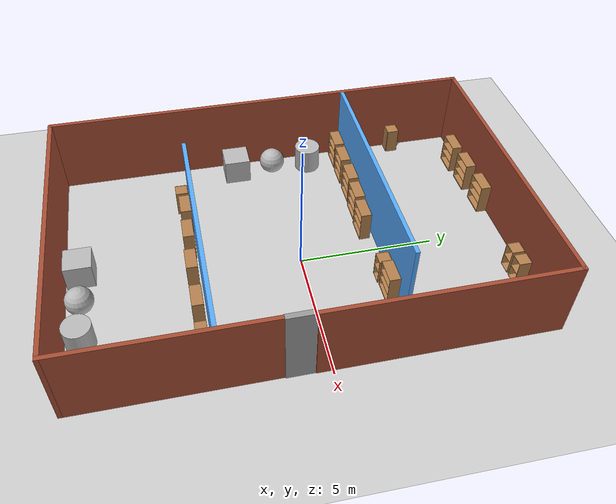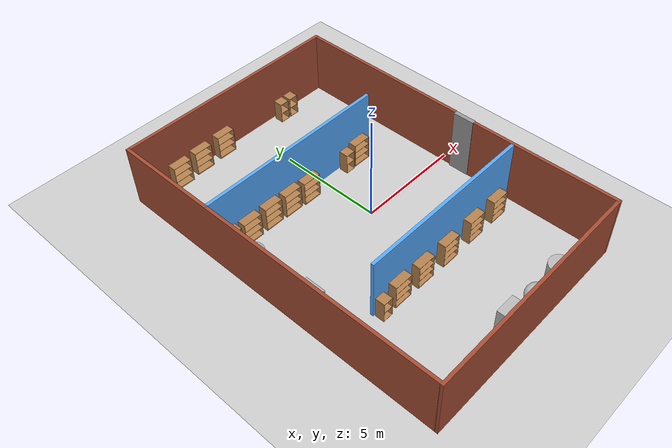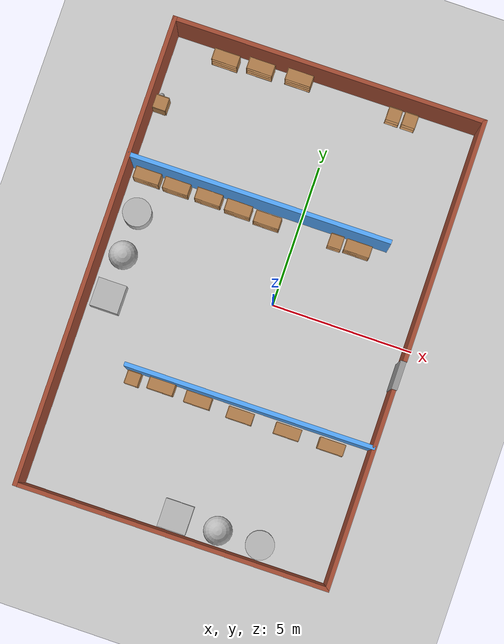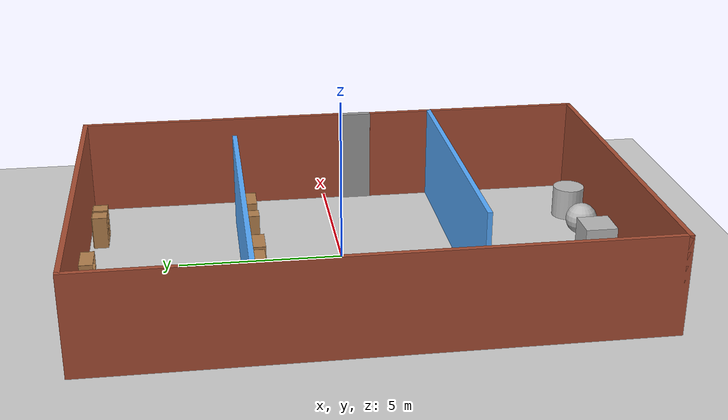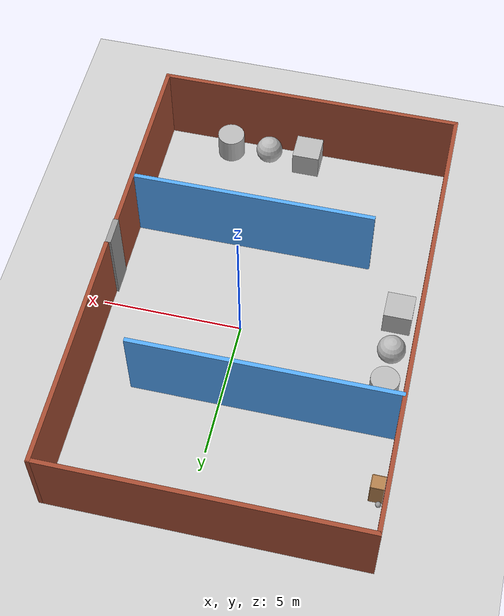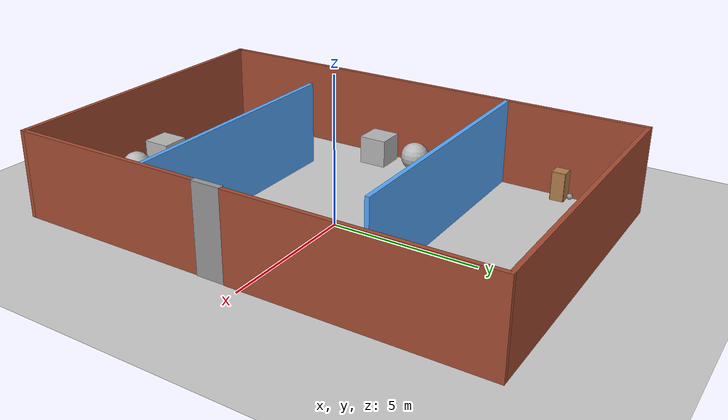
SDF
<sdf version="1.6">
 <world name="default">
  <plugin name="welcome_message" filename="libwelcome_message.so"/>
  <light name="sun" type="directional">
   <pose>0 0 10 0 -0 0</pose>
   <diffuse>0.8 0.8 0.8 1</diffuse>
   <specular>0.2 0.2 0.2 1</specular>
   <attenuation>
    <range>1000</range>
    <constant>0.9</constant>
    <linear>0.01</linear>
    <quadratic>0.001</quadratic>
   </attenuation>
   <direction>-0.5 0.1 -0.9</direction>
  </light>
  <model name="ground_plane">
   <static>1</static>
   <link name="link">
    <collision name="collision">
     <geometry><plane><normal>0 0 1</normal><size>100 100</size></plane></geometry>
     <surface>
      <contact><collide_bitmask>65535</collide_bitmask></contact>
      <friction><ode><mu>100</mu><mu2>50</mu2></ode></friction>
     </surface>
    </collision>
    <visual name="visual">
     <cast_shadows>0</cast_shadows>
     <geometry><plane><normal>0 0 1</normal><size>100 100</size></plane></geometry>
     <material>
      <script><uri>file://media/materials/scripts/gazebo.material</uri><name>Gazebo/Grey</name></script>
     </material>
    </visual>
   </link>
  </model>
  <gravity>0 0 -9.8</gravity>
  <magnetic_field>6e-06 2.3e-05 -4.2e-05</magnetic_field>
  <atmosphere type="adiabatic"/>
  <physics name="default_physics" default="0" type="ode">
   <max_step_size>0.001</max_step_size>
   <real_time_factor>1</real_time_factor>
   <real_time_update_rate>1000</real_time_update_rate>
  </physics>
  <scene><ambient>0.4 0.4 0.4 1</ambient><background>0.7 0.7 0.7 1</background><shadows>1</shadows></scene>
  <spherical_coordinates>
   <surface_model>EARTH_WGS84</surface_model>
   <latitude_deg>0</latitude_deg>
   <longitude_deg>0</longitude_deg>
   <elevation>0</elevation>
   <heading_deg>0</heading_deg>
  </spherical_coordinates>
  <model name="dragonHouse">
   <pose>-0.668267 -0.331134 0 0 -0 1.57463</pose>
   <link name="Door_0">
    <collision name="Door_0_Collision">
     <geometry><box><size>0.990813 0.2 3</size></box></geometry>
     <pose>0 0 1.5 0 -0 0</pose>
    </collision>
    <visual name="Door_0_Visual">
     <pose>0 0 1.5 0 -0 0</pose>
     <geometry><box><size>0.990813 0.2 3</size></box></geometry>
     <material>
      <script><uri>file://media/materials/scripts/gazebo.material</uri><name>Gazebo/Grey</name></script>
     </material>
    </visual>
    <pose>-0.750469 -5.40399 0 0 -0 0.00282</pose>
   </link>
   <link name="Wall_0">
    <collision name="Wall_0_Collision">
     <geometry><box><size>7 0.15 3</size></box></geometry>
     <pose>0 0 1.5 0 -0 0</pose>
    </collision>
    <visual name="Wall_0_Visual">
     <pose>0 0 1.5 0 -0 0</pose>
     <geometry><box><size>7 0.15 3</size></box></geometry>
     <material>
      <script><uri>file://media/materials/scripts/gazebo.material</uri><name>Gazebo/Bricks</name></script>
      <ambient>1 1 1 1</ambient>
     </material>
     <meta><layer>0</layer></meta>
    </visual>
    <pose>-4.75 -5.402 0 0 -0 3.14159</pose>
   </link>
   <link name="Wall_1">
    <collision name="Wall_1_Collision">
     <geometry><box><size>11 0.15 3</size></box></geometry>
     <pose>0 0 1.5 0 -0 0</pose>
    </collision>
    <visual name="Wall_1_Visual">
     <pose>0 0 1.5 0 -0 0</pose>
     <geometry><box><size>11 0.15 3</size></box></geometry>
     <material>
      <script><uri>file://media/materials/scripts/gazebo.material</uri><name>Gazebo/Bricks</name></script>
      <ambient>1 1 1 1</ambient>
     </material>
     <meta><layer>0</layer></meta>
    </visual>
    <pose>-8.175 0.023 0 0 -0 1.5708</pose>
   </link>
   <link name="Wall_10">
    <collision name="Wall_10_Collision">
     <geometry><box><size>9.25 0.15 3</size></box></geometry>
     <pose>0 0 1.5 0 -0 0</pose>
    </collision>
    <visual name="Wall_10_Visual">
     <pose>0 0 1.5 0 -0 0</pose>
     <geometry><box><size>9.25 0.15 3</size></box></geometry>
     <material>
      <script><uri>file://media/materials/scripts/gazebo.material</uri><name>Gazebo/Grey</name></script>
      <ambient>0.333333 0.666667 1 1</ambient>
     </material>
     <meta><layer>0</layer></meta>
    </visual>
    <pose>3.371 0.836 0 0 0 -1.5708</pose>
   </link>
   <link name="Wall_2">
    <collision name="Wall_2_Collision">
     <geometry><box><size>16.5 0.15 3</size></box></geometry>
     <pose>0 0 1.5 0 -0 0</pose>
    </collision>
    <visual name="Wall_2_Visual">
     <pose>0 0 1.5 0 -0 0</pose>
     <geometry><box><size>16.5 0.15 3</size></box></geometry>
     <material>
      <script><uri>file://media/materials/scripts/gazebo.material</uri><name>Gazebo/Bricks</name></script>
      <ambient>1 1 1 1</ambient>
     </material>
     <meta><layer>0</layer></meta>
    </visual>
    <pose>0 5.448 0 0 -0 0</pose>
   </link>
   <link name="Wall_3">
    <collision name="Wall_3_Collision">
     <geometry><box><size>11.046 0.15 3</size></box></geometry>
     <pose>0 0 1.5 0 -0 0</pose>
    </collision>
    <visual name="Wall_3_Visual">
     <pose>0 0 1.5 0 -0 0</pose>
     <geometry><box><size>11.046 0.15 3</size></box></geometry>
     <material>
      <script><uri>file://media/materials/scripts/gazebo.material</uri><name>Gazebo/Bricks</name></script>
      <ambient>1 1 1 1</ambient>
     </material>
     <meta><layer>0</layer></meta>
    </visual>
    <pose>8.175 0 0 0 0 -1.5708</pose>
   </link>
   <link name="Wall_4">
    <collision name="Wall_4_Collision">
     <geometry><box><size>8.5 0.15 3</size></box></geometry>
     <pose>0 0 1.5 0 -0 0</pose>
    </collision>
    <visual name="Wall_4_Visual">
     <pose>0 0 1.5 0 -0 0</pose>
     <geometry><box><size>8.5 0.15 3</size></box></geometry>
     <material>
      <script><uri>file://media/materials/scripts/gazebo.material</uri><name>Gazebo/Bricks</name></script>
      <ambient>1 1 1 1</ambient>
     </material>
     <meta><layer>0</layer></meta>
    </visual>
    <pose>4 -5.448 0 0 -0 3.14159</pose>
   </link>
   <link name="Wall_8">
    <collision name="Wall_8_Collision">
     <geometry><box><size>8.75 0.15 3</size></box></geometry>
     <pose>0 0 1.5 0 -0 0</pose>
    </collision>
    <visual name="Wall_8_Visual">
     <pose>0 0 1.5 0 -0 0</pose>
     <geometry><box><size>8.75 0.15 3</size></box></geometry>
     <material>
      <script><uri>file://media/materials/scripts/gazebo.material</uri><name>Gazebo/Grey</name></script>
      <ambient>0.333333 0.666667 1 1</ambient>
     </material>
     <meta><layer>0</layer></meta>
    </visual>
    <pose>-3.276 -1.053 0 0 0 -1.5708</pose>
   </link>
   <static>1</static>
  </model>
  <model name="bookshelf">
   <static>1</static>
   <link name="link">
    <inertial><mass>1</mass></inertial>
    <collision name="back">
     <pose>0 0.005 0.6 0 -0 0</pose>
     <geometry><box><size>0.9 0.01 1.2</size></box></geometry>
    </collision>
    <visual name="visual1">
     <pose>0 0.005 0.6 0 -0 0</pose>
     <geometry><box><size>0.9 0.01 1.2</size></box></geometry>
     <material>
      <script><uri>file://media/materials/scripts/gazebo.material</uri><name>Gazebo/Wood</name></script>
     </material>
    </visual>
    <collision name="left_side">
     <pose>0.45 -0.195 0.6 0 -0 0</pose>
     <geometry><box><size>0.02 0.4 1.2</size></box></geometry>
    </collision>
    <visual name="visual2">
     <pose>0.45 -0.195 0.6 0 -0 0</pose>
     <geometry><box><size>0.02 0.4 1.2</size></box></geometry>
     <material>
      <script><uri>file://media/materials/scripts/gazebo.material</uri><name>Gazebo/Wood</name></script>
     </material>
    </visual>
    <collision name="right_side">
     <pose>-0.45 -0.195 0.6 0 -0 0</pose>
     <geometry><box><size>0.02 0.4 1.2</size></box></geometry>
    </collision>
    <visual name="visual3">
     <pose>-0.45 -0.195 0.6 0 -0 0</pose>
     <geometry><box><size>0.02 0.4 1.2</size></box></geometry>
     <material>
      <script><uri>file://media/materials/scripts/gazebo.material</uri><name>Gazebo/Wood</name></script>
     </material>
    </visual>
    <collision name="bottom">
     <pose>0 -0.195 0.03 0 -0 0</pose>
     <geometry><box><size>0.88 0.4 0.06</size></box></geometry>
    </collision>
    <visual name="visual4">
     <pose>0 -0.195 0.03 0 -0 0</pose>
     <geometry><box><size>0.88 0.4 0.06</size></box></geometry>
     <material>
      <script><uri>file://media/materials/scripts/gazebo.material</uri><name>Gazebo/Wood</name></script>
     </material>
    </visual>
    <collision name="top">
     <pose>0 -0.195 1.19 0 -0 0</pose>
     <geometry><box><size>0.88 0.4 0.02</size></box></geometry>
    </collision>
    <visual name="visual5">
     <pose>0 -0.195 1.19 0 -0 0</pose>
     <geometry><box><size>0.88 0.4 0.02</size></box></geometry>
     <material>
      <script><uri>file://media/materials/scripts/gazebo.material</uri><name>Gazebo/Wood</name></script>
     </material>
    </visual>
    <collision name="low_shelf">
     <pose>0 -0.195 0.43 0 -0 0</pose>
     <geometry><box><size>0.88 0.4 0.02</size></box></geometry>
    </collision>
    <visual name="visual6">
     <pose>0 -0.195 0.43 0 -0 0</pose>
     <geometry><box><size>0.88 0.4 0.02</size></box></geometry>
     <material>
      <script><uri>file://media/materials/scripts/gazebo.material</uri><name>Gazebo/Wood</name></script>
     </material>
    </visual>
    <collision name="high_shelf">
     <pose>0 -0.195 0.8 0 -0 0</pose>
     <geometry><box><size>0.88 0.4 0.02</size></box></geometry>
    </collision>
    <visual name="visual7">
     <pose>0 -0.195 0.8 0 -0 0</pose>
     <geometry><box><size>0.88 0.4 0.02</size></box></geometry>
     <material>
      <script><uri>file://media/materials/scripts/gazebo.material</uri><name>Gazebo/Wood</name></script>
     </material>
    </visual>
   </link>
   <pose>-5.43016 2.91129 0 0 -0 0</pose>
  </model>
  <model name="cabinet">
   <static>1</static>
   <link name="cabinet_bottom_plate">
    <inertial>
     <pose>0 0 -1 0 -0 0</pose>
     <inertia><ixx>2.05</ixx><ixy>0</ixy><ixz>0</ixz><iyy>2.05</iyy><iyz>0</iyz><izz>2.05</izz></inertia>
     <mass>25</mass>
    </inertial>
    <collision name="cabinet_bottom_plate_geom">
     <pose>0 0 0.01 0 -0 0</pose>
     <geometry><box><size>0.45 0.45 0.02</size></box></geometry>
    </collision>
    <visual name="cabinet_bottom_plate_geom_visual">
     <pose>0 0 0.01 0 -0 0</pose>
     <geometry><box><size>0.45 0.45 0.02</size></box></geometry>
     <material>
      <script><uri>file://media/materials/scripts/gazebo.material</uri><name>Gazebo/Wood</name></script>
     </material>
    </visual>
    <collision name="cabinet_bottom_plate_geom_cabinet_back_plate">
     <pose>0.235 0 0.51 0 -0 0</pose>
     <geometry><box><size>0.02 0.45 1.02</size></box></geometry>
    </collision>
    <visual name="cabinet_bottom_plate_geom_cabinet_back_plate_visual">
     <pose>0.235 0 0.51 0 -0 0</pose>
     <geometry><box><size>0.02 0.45 1.02</size></box></geometry>
     <material>
      <script><uri>file://media/materials/scripts/gazebo.material</uri><name>Gazebo/Wood</name></script>
     </material>
    </visual>
    <collision name="cabinet_bottom_plate_geom_cabinet_left_plate">
     <pose>0 0.235 0.51 0 -0 0</pose>
     <geometry><box><size>0.45 0.02 1.02</size></box></geometry>
    </collision>
    <visual name="cabinet_bottom_plate_geom_cabinet_left_plate_visual">
     <pose>0 0.235 0.51 0 -0 0</pose>
     <geometry><box><size>0.45 0.02 1.02</size></box></geometry>
     <material>
      <script><uri>file://media/materials/scripts/gazebo.material</uri><name>Gazebo/Wood</name></script>
     </material>
    </visual>
    <collision name="cabinet_bottom_plate_geom_cabinet_middle_plate">
     <pose>0 0 0.51 0 -0 0</pose>
     <geometry><box><size>0.45 0.45 0.02</size></box></geometry>
    </collision>
    <visual name="cabinet_bottom_plate_geom_cabinet_middle_plate_visual">
     <pose>0 0 0.51 0 -0 0</pose>
     <geometry><box><size>0.45 0.45 0.02</size></box></geometry>
     <material>
      <script><uri>file://media/materials/scripts/gazebo.material</uri><name>Gazebo/Wood</name></script>
     </material>
    </visual>
    <collision name="cabinet_bottom_plate_geom_cabinet_right_plate">
     <pose>0 -0.235 0.51 0 -0 0</pose>
     <geometry><box><size>0.45 0.02 1.02</size></box></geometry>
    </collision>
    <visual name="cabinet_bottom_plate_geom_cabinet_right_plate_visual">
     <pose>0 -0.235 0.51 0 -0 0</pose>
     <geometry><box><size>0.45 0.02 1.02</size></box></geometry>
     <material>
      <script><uri>file://media/materials/scripts/gazebo.material</uri><name>Gazebo/Wood</name></script>
     </material>
    </visual>
    <collision name="cabinet_bottom_plate_geom_cabinet_top_plate">
     <pose>0 0 1.01 0 -0 0</pose>
     <geometry><box><size>0.45 0.45 0.02</size></box></geometry>
    </collision>
    <visual name="cabinet_bottom_plate_geom_cabinet_top_plate_visual">
     <pose>0 0 1.01 0 -0 0</pose>
     <geometry><box><size>0.45 0.45 0.02</size></box></geometry>
     <material>
      <script><uri>file://media/materials/scripts/gazebo.material</uri><name>Gazebo/Wood</name></script>
     </material>
    </visual>
   </link>
   <pose>-5.82301 5.24681 0 0 -0 0</pose>
  </model>
  <model name="my_ball">
   <link name="link_0">
    <inertial>
     <mass>1</mass>
     <inertia><ixx>0.1</ixx><ixy>0</ixy><ixz>0</ixz><iyy>0.1</iyy><iyz>0</iyz><izz>0.1</izz></inertia>
    </inertial>
    <visual name="visual">
     <geometry><sphere><radius>0.1</radius></sphere></geometry>
     <material>
      <lighting>1</lighting>
      <script><uri>file://media/materials/scripts/gazebo.material</uri><name>Gazebo/Grey</name></script>
      <shader type="pixel"><normal_map>__default__</normal_map></shader>
      <ambient>1 1 1 1</ambient>
      <diffuse>1 1 1 1</diffuse>
      <specular>1 1 1 1</specular>
      <emissive>1 1 1 1</emissive>
     </material>
    </visual>
    <collision name="collision">
     <geometry><sphere><radius>0.1</radius></sphere></geometry>
     <surface>
      <friction>
       <ode><mu>1</mu><mu2>1</mu2><fdir1>0 0 0</fdir1><slip1>0</slip1><slip2>0</slip2></ode>
       <torsional>
        <coefficient>1</coefficient>
        <patch_radius>0</patch_radius>
        <surface_radius>0</surface_radius>
        <use_patch_radius>1</use_patch_radius>
        <ode><slip>0</slip></ode>
       </torsional>
      </friction>
      <bounce><restitution_coefficient>0</restitution_coefficient><threshold>1e+06</threshold></bounce>
      <contact>
       <collide_without_contact>0</collide_without_contact>
       <collide_without_contact_bitmask>1</collide_without_contact_bitmask>
       <collide_bitmask>1</collide_bitmask>
       <ode>
        <soft_cfm>0</soft_cfm>
        <soft_erp>0.2</soft_erp>
        <kp>1e+13</kp>
        <kd>1</kd>
        <max_vel>0.01</max_vel>
        <min_depth>0</min_depth>
       </ode>
       <bullet>
        <split_impulse>1</split_impulse>
        <split_impulse_penetration_threshold>-0.01</split_impulse_penetration_threshold>
        <soft_cfm>0</soft_cfm>
        <soft_erp>0.2</soft_erp>
        <kp>1e+13</kp>
        <kd>1</kd>
       </bullet>
      </contact>
     </surface>
    </collision>
   </link>
   <static>0</static>
   <pose>-5.94046 5.59184 0.1 -0.373632 -0.842459 2.33568</pose>
  </model>
  <model name="bookshelf_clone">
   <static>1</static>
   <link name="link">
    <inertial><mass>1</mass></inertial>
    <collision name="back">
     <pose>0 0.005 0.6 0 -0 0</pose>
     <geometry><box><size>0.9 0.01 1.2</size></box></geometry>
    </collision>
    <visual name="visual1">
     <pose>0 0.005 0.6 0 -0 0</pose>
     <geometry><box><size>0.9 0.01 1.2</size></box></geometry>
     <material>
      <script><uri>file://media/materials/scripts/gazebo.material</uri><name>Gazebo/Wood</name></script>
     </material>
    </visual>
    <collision name="left_side">
     <pose>0.45 -0.195 0.6 0 -0 0</pose>
     <geometry><box><size>0.02 0.4 1.2</size></box></geometry>
    </collision>
    <visual name="visual2">
     <pose>0.45 -0.195 0.6 0 -0 0</pose>
     <geometry><box><size>0.02 0.4 1.2</size></box></geometry>
     <material>
      <script><uri>file://media/materials/scripts/gazebo.material</uri><name>Gazebo/Wood</name></script>
     </material>
    </visual>
    <collision name="right_side">
     <pose>-0.45 -0.195 0.6 0 -0 0</pose>
     <geometry><box><size>0.02 0.4 1.2</size></box></geometry>
    </collision>
    <visual name="visual3">
     <pose>-0.45 -0.195 0.6 0 -0 0</pose>
     <geometry><box><size>0.02 0.4 1.2</size></box></geometry>
     <material>
      <script><uri>file://media/materials/scripts/gazebo.material</uri><name>Gazebo/Wood</name></script>
     </material>
    </visual>
    <collision name="bottom">
     <pose>0 -0.195 0.03 0 -0 0</pose>
     <geometry><box><size>0.88 0.4 0.06</size></box></geometry>
    </collision>
    <visual name="visual4">
     <pose>0 -0.195 0.03 0 -0 0</pose>
     <geometry><box><size>0.88 0.4 0.06</size></box></geometry>
     <material>
      <script><uri>file://media/materials/scripts/gazebo.material</uri><name>Gazebo/Wood</name></script>
     </material>
    </visual>
    <collision name="top">
     <pose>0 -0.195 1.19 0 -0 0</pose>
     <geometry><box><size>0.88 0.4 0.02</size></box></geometry>
    </collision>
    <visual name="visual5">
     <pose>0 -0.195 1.19 0 -0 0</pose>
     <geometry><box><size>0.88 0.4 0.02</size></box></geometry>
     <material>
      <script><uri>file://media/materials/scripts/gazebo.material</uri><name>Gazebo/Wood</name></script>
     </material>
    </visual>
    <collision name="low_shelf">
     <pose>0 -0.195 0.43 0 -0 0</pose>
     <geometry><box><size>0.88 0.4 0.02</size></box></geometry>
    </collision>
    <visual name="visual6">
     <pose>0 -0.195 0.43 0 -0 0</pose>
     <geometry><box><size>0.88 0.4 0.02</size></box></geometry>
     <material>
      <script><uri>file://media/materials/scripts/gazebo.material</uri><name>Gazebo/Wood</name></script>
     </material>
    </visual>
    <collision name="high_shelf">
     <pose>0 -0.195 0.8 0 -0 0</pose>
     <geometry><box><size>0.88 0.4 0.02</size></box></geometry>
    </collision>
    <visual name="visual7">
     <pose>0 -0.195 0.8 0 -0 0</pose>
     <geometry><box><size>0.88 0.4 0.02</size></box></geometry>
     <material>
      <script><uri>file://media/materials/scripts/gazebo.material</uri><name>Gazebo/Wood</name></script>
     </material>
    </visual>
   </link>
   <pose>-4.37438 2.89706 0 0 -0 0</pose>
  </model>
  <model name="bookshelf_clone_0">
   <static>1</static>
   <link name="link">
    <inertial><mass>1</mass></inertial>
    <collision name="back">
     <pose>0 0.005 0.6 0 -0 0</pose>
     <geometry><box><size>0.9 0.01 1.2</size></box></geometry>
    </collision>
    <visual name="visual1">
     <pose>0 0.005 0.6 0 -0 0</pose>
     <geometry><box><size>0.9 0.01 1.2</size></box></geometry>
     <material>
      <script><uri>file://media/materials/scripts/gazebo.material</uri><name>Gazebo/Wood</name></script>
     </material>
    </visual>
    <collision name="left_side">
     <pose>0.45 -0.195 0.6 0 -0 0</pose>
     <geometry><box><size>0.02 0.4 1.2</size></box></geometry>
    </collision>
    <visual name="visual2">
     <pose>0.45 -0.195 0.6 0 -0 0</pose>
     <geometry><box><size>0.02 0.4 1.2</size></box></geometry>
     <material>
      <script><uri>file://media/materials/scripts/gazebo.material</uri><name>Gazebo/Wood</name></script>
     </material>
    </visual>
    <collision name="right_side">
     <pose>-0.45 -0.195 0.6 0 -0 0</pose>
     <geometry><box><size>0.02 0.4 1.2</size></box></geometry>
    </collision>
    <visual name="visual3">
     <pose>-0.45 -0.195 0.6 0 -0 0</pose>
     <geometry><box><size>0.02 0.4 1.2</size></box></geometry>
     <material>
      <script><uri>file://media/materials/scripts/gazebo.material</uri><name>Gazebo/Wood</name></script>
     </material>
    </visual>
    <collision name="bottom">
     <pose>0 -0.195 0.03 0 -0 0</pose>
     <geometry><box><size>0.88 0.4 0.06</size></box></geometry>
    </collision>
    <visual name="visual4">
     <pose>0 -0.195 0.03 0 -0 0</pose>
     <geometry><box><size>0.88 0.4 0.06</size></box></geometry>
     <material>
      <script><uri>file://media/materials/scripts/gazebo.material</uri><name>Gazebo/Wood</name></script>
     </material>
    </visual>
    <collision name="top">
     <pose>0 -0.195 1.19 0 -0 0</pose>
     <geometry><box><size>0.88 0.4 0.02</size></box></geometry>
    </collision>
    <visual name="visual5">
     <pose>0 -0.195 1.19 0 -0 0</pose>
     <geometry><box><size>0.88 0.4 0.02</size></box></geometry>
     <material>
      <script><uri>file://media/materials/scripts/gazebo.material</uri><name>Gazebo/Wood</name></script>
     </material>
    </visual>
    <collision name="low_shelf">
     <pose>0 -0.195 0.43 0 -0 0</pose>
     <geometry><box><size>0.88 0.4 0.02</size></box></geometry>
    </collision>
    <visual name="visual6">
     <pose>0 -0.195 0.43 0 -0 0</pose>
     <geometry><box><size>0.88 0.4 0.02</size></box></geometry>
     <material>
      <script><uri>file://media/materials/scripts/gazebo.material</uri><name>Gazebo/Wood</name></script>
     </material>
    </visual>
    <collision name="high_shelf">
     <pose>0 -0.195 0.8 0 -0 0</pose>
     <geometry><box><size>0.88 0.4 0.02</size></box></geometry>
    </collision>
    <visual name="visual7">
     <pose>0 -0.195 0.8 0 -0 0</pose>
     <geometry><box><size>0.88 0.4 0.02</size></box></geometry>
     <material>
      <script><uri>file://media/materials/scripts/gazebo.material</uri><name>Gazebo/Wood</name></script>
     </material>
    </visual>
   </link>
   <pose>-3.22108 2.90448 0 0 -0 0</pose>
  </model>
  <model name="bookshelf_clone_1">
   <static>1</static>
   <link name="link">
    <inertial><mass>1</mass></inertial>
    <collision name="back">
     <pose>0 0.005 0.6 0 -0 0</pose>
     <geometry><box><size>0.9 0.01 1.2</size></box></geometry>
    </collision>
    <visual name="visual1">
     <pose>0 0.005 0.6 0 -0 0</pose>
     <geometry><box><size>0.9 0.01 1.2</size></box></geometry>
     <material>
      <script><uri>file://media/materials/scripts/gazebo.material</uri><name>Gazebo/Wood</name></script>
     </material>
    </visual>
    <collision name="left_side">
     <pose>0.45 -0.195 0.6 0 -0 0</pose>
     <geometry><box><size>0.02 0.4 1.2</size></box></geometry>
    </collision>
    <visual name="visual2">
     <pose>0.45 -0.195 0.6 0 -0 0</pose>
     <geometry><box><size>0.02 0.4 1.2</size></box></geometry>
     <material>
      <script><uri>file://media/materials/scripts/gazebo.material</uri><name>Gazebo/Wood</name></script>
     </material>
    </visual>
    <collision name="right_side">
     <pose>-0.45 -0.195 0.6 0 -0 0</pose>
     <geometry><box><size>0.02 0.4 1.2</size></box></geometry>
    </collision>
    <visual name="visual3">
     <pose>-0.45 -0.195 0.6 0 -0 0</pose>
     <geometry><box><size>0.02 0.4 1.2</size></box></geometry>
     <material>
      <script><uri>file://media/materials/scripts/gazebo.material</uri><name>Gazebo/Wood</name></script>
     </material>
    </visual>
    <collision name="bottom">
     <pose>0 -0.195 0.03 0 -0 0</pose>
     <geometry><box><size>0.88 0.4 0.06</size></box></geometry>
    </collision>
    <visual name="visual4">
     <pose>0 -0.195 0.03 0 -0 0</pose>
     <geometry><box><size>0.88 0.4 0.06</size></box></geometry>
     <material>
      <script><uri>file://media/materials/scripts/gazebo.material</uri><name>Gazebo/Wood</name></script>
     </material>
    </visual>
    <collision name="top">
     <pose>0 -0.195 1.19 0 -0 0</pose>
     <geometry><box><size>0.88 0.4 0.02</size></box></geometry>
    </collision>
    <visual name="visual5">
     <pose>0 -0.195 1.19 0 -0 0</pose>
     <geometry><box><size>0.88 0.4 0.02</size></box></geometry>
     <material>
      <script><uri>file://media/materials/scripts/gazebo.material</uri><name>Gazebo/Wood</name></script>
     </material>
    </visual>
    <collision name="low_shelf">
     <pose>0 -0.195 0.43 0 -0 0</pose>
     <geometry><box><size>0.88 0.4 0.02</size></box></geometry>
    </collision>
    <visual name="visual6">
     <pose>0 -0.195 0.43 0 -0 0</pose>
     <geometry><box><size>0.88 0.4 0.02</size></box></geometry>
     <material>
      <script><uri>file://media/materials/scripts/gazebo.material</uri><name>Gazebo/Wood</name></script>
     </material>
    </visual>
    <collision name="high_shelf">
     <pose>0 -0.195 0.8 0 -0 0</pose>
     <geometry><box><size>0.88 0.4 0.02</size></box></geometry>
    </collision>
    <visual name="visual7">
     <pose>0 -0.195 0.8 0 -0 0</pose>
     <geometry><box><size>0.88 0.4 0.02</size></box></geometry>
     <material>
      <script><uri>file://media/materials/scripts/gazebo.material</uri><name>Gazebo/Wood</name></script>
     </material>
    </visual>
   </link>
   <pose>-2.14045 2.86293 0 0 -0 0</pose>
  </model>
  <model name="bookshelf_clone_2">
   <static>1</static>
   <link name="link">
    <inertial><mass>1</mass></inertial>
    <collision name="back">
     <pose>0 0.005 0.6 0 -0 0</pose>
     <geometry><box><size>0.9 0.01 1.2</size></box></geometry>
    </collision>
    <visual name="visual1">
     <pose>0 0.005 0.6 0 -0 0</pose>
     <geometry><box><size>0.9 0.01 1.2</size></box></geometry>
     <material>
      <script><uri>file://media/materials/scripts/gazebo.material</uri><name>Gazebo/Wood</name></script>
     </material>
    </visual>
    <collision name="left_side">
     <pose>0.45 -0.195 0.6 0 -0 0</pose>
     <geometry><box><size>0.02 0.4 1.2</size></box></geometry>
    </collision>
    <visual name="visual2">
     <pose>0.45 -0.195 0.6 0 -0 0</pose>
     <geometry><box><size>0.02 0.4 1.2</size></box></geometry>
     <material>
      <script><uri>file://media/materials/scripts/gazebo.material</uri><name>Gazebo/Wood</name></script>
     </material>
    </visual>
    <collision name="right_side">
     <pose>-0.45 -0.195 0.6 0 -0 0</pose>
     <geometry><box><size>0.02 0.4 1.2</size></box></geometry>
    </collision>
    <visual name="visual3">
     <pose>-0.45 -0.195 0.6 0 -0 0</pose>
     <geometry><box><size>0.02 0.4 1.2</size></box></geometry>
     <material>
      <script><uri>file://media/materials/scripts/gazebo.material</uri><name>Gazebo/Wood</name></script>
     </material>
    </visual>
    <collision name="bottom">
     <pose>0 -0.195 0.03 0 -0 0</pose>
     <geometry><box><size>0.88 0.4 0.06</size></box></geometry>
    </collision>
    <visual name="visual4">
     <pose>0 -0.195 0.03 0 -0 0</pose>
     <geometry><box><size>0.88 0.4 0.06</size></box></geometry>
     <material>
      <script><uri>file://media/materials/scripts/gazebo.material</uri><name>Gazebo/Wood</name></script>
     </material>
    </visual>
    <collision name="top">
     <pose>0 -0.195 1.19 0 -0 0</pose>
     <geometry><box><size>0.88 0.4 0.02</size></box></geometry>
    </collision>
    <visual name="visual5">
     <pose>0 -0.195 1.19 0 -0 0</pose>
     <geometry><box><size>0.88 0.4 0.02</size></box></geometry>
     <material>
      <script><uri>file://media/materials/scripts/gazebo.material</uri><name>Gazebo/Wood</name></script>
     </material>
    </visual>
    <collision name="low_shelf">
     <pose>0 -0.195 0.43 0 -0 0</pose>
     <geometry><box><size>0.88 0.4 0.02</size></box></geometry>
    </collision>
    <visual name="visual6">
     <pose>0 -0.195 0.43 0 -0 0</pose>
     <geometry><box><size>0.88 0.4 0.02</size></box></geometry>
     <material>
      <script><uri>file://media/materials/scripts/gazebo.material</uri><name>Gazebo/Wood</name></script>
     </material>
    </visual>
    <collision name="high_shelf">
     <pose>0 -0.195 0.8 0 -0 0</pose>
     <geometry><box><size>0.88 0.4 0.02</size></box></geometry>
    </collision>
    <visual name="visual7">
     <pose>0 -0.195 0.8 0 -0 0</pose>
     <geometry><box><size>0.88 0.4 0.02</size></box></geometry>
     <material>
      <script><uri>file://media/materials/scripts/gazebo.material</uri><name>Gazebo/Wood</name></script>
     </material>
    </visual>
   </link>
   <pose>-1.08409 2.80907 0 0 -0 0</pose>
  </model>
  <model name="bookshelf_clone_3">
   <static>1</static>
   <link name="link">
    <inertial><mass>1</mass></inertial>
    <collision name="back">
     <pose>0 0.005 0.6 0 -0 0</pose>
     <geometry><box><size>0.9 0.01 1.2</size></box></geometry>
    </collision>
    <visual name="visual1">
     <pose>0 0.005 0.6 0 -0 0</pose>
     <geometry><box><size>0.9 0.01 1.2</size></box></geometry>
     <material>
      <script><uri>file://media/materials/scripts/gazebo.material</uri><name>Gazebo/Wood</name></script>
     </material>
    </visual>
    <collision name="left_side">
     <pose>0.45 -0.195 0.6 0 -0 0</pose>
     <geometry><box><size>0.02 0.4 1.2</size></box></geometry>
    </collision>
    <visual name="visual2">
     <pose>0.45 -0.195 0.6 0 -0 0</pose>
     <geometry><box><size>0.02 0.4 1.2</size></box></geometry>
     <material>
      <script><uri>file://media/materials/scripts/gazebo.material</uri><name>Gazebo/Wood</name></script>
     </material>
    </visual>
    <collision name="right_side">
     <pose>-0.45 -0.195 0.6 0 -0 0</pose>
     <geometry><box><size>0.02 0.4 1.2</size></box></geometry>
    </collision>
    <visual name="visual3">
     <pose>-0.45 -0.195 0.6 0 -0 0</pose>
     <geometry><box><size>0.02 0.4 1.2</size></box></geometry>
     <material>
      <script><uri>file://media/materials/scripts/gazebo.material</uri><name>Gazebo/Wood</name></script>
     </material>
    </visual>
    <collision name="bottom">
     <pose>0 -0.195 0.03 0 -0 0</pose>
     <geometry><box><size>0.88 0.4 0.06</size></box></geometry>
    </collision>
    <visual name="visual4">
     <pose>0 -0.195 0.03 0 -0 0</pose>
     <geometry><box><size>0.88 0.4 0.06</size></box></geometry>
     <material>
      <script><uri>file://media/materials/scripts/gazebo.material</uri><name>Gazebo/Wood</name></script>
     </material>
    </visual>
    <collision name="top">
     <pose>0 -0.195 1.19 0 -0 0</pose>
     <geometry><box><size>0.88 0.4 0.02</size></box></geometry>
    </collision>
    <visual name="visual5">
     <pose>0 -0.195 1.19 0 -0 0</pose>
     <geometry><box><size>0.88 0.4 0.02</size></box></geometry>
     <material>
      <script><uri>file://media/materials/scripts/gazebo.material</uri><name>Gazebo/Wood</name></script>
     </material>
    </visual>
    <collision name="low_shelf">
     <pose>0 -0.195 0.43 0 -0 0</pose>
     <geometry><box><size>0.88 0.4 0.02</size></box></geometry>
    </collision>
    <visual name="visual6">
     <pose>0 -0.195 0.43 0 -0 0</pose>
     <geometry><box><size>0.88 0.4 0.02</size></box></geometry>
     <material>
      <script><uri>file://media/materials/scripts/gazebo.material</uri><name>Gazebo/Wood</name></script>
     </material>
    </visual>
    <collision name="high_shelf">
     <pose>0 -0.195 0.8 0 -0 0</pose>
     <geometry><box><size>0.88 0.4 0.02</size></box></geometry>
    </collision>
    <visual name="visual7">
     <pose>0 -0.195 0.8 0 -0 0</pose>
     <geometry><box><size>0.88 0.4 0.02</size></box></geometry>
     <material>
      <script><uri>file://media/materials/scripts/gazebo.material</uri><name>Gazebo/Wood</name></script>
     </material>
    </visual>
   </link>
   <pose>-1.62647 7.75744 0 0 -0 0</pose>
  </model>
  <model name="bookshelf_clone_4">
   <static>1</static>
   <link name="link">
    <inertial><mass>1</mass></inertial>
    <collision name="back">
     <pose>0 0.005 0.6 0 -0 0</pose>
     <geometry><box><size>0.9 0.01 1.2</size></box></geometry>
    </collision>
    <visual name="visual1">
     <pose>0 0.005 0.6 0 -0 0</pose>
     <geometry><box><size>0.9 0.01 1.2</size></box></geometry>
     <material>
      <script><uri>file://media/materials/scripts/gazebo.material</uri><name>Gazebo/Wood</name></script>
     </material>
    </visual>
    <collision name="left_side">
     <pose>0.45 -0.195 0.6 0 -0 0</pose>
     <geometry><box><size>0.02 0.4 1.2</size></box></geometry>
    </collision>
    <visual name="visual2">
     <pose>0.45 -0.195 0.6 0 -0 0</pose>
     <geometry><box><size>0.02 0.4 1.2</size></box></geometry>
     <material>
      <script><uri>file://media/materials/scripts/gazebo.material</uri><name>Gazebo/Wood</name></script>
     </material>
    </visual>
    <collision name="right_side">
     <pose>-0.45 -0.195 0.6 0 -0 0</pose>
     <geometry><box><size>0.02 0.4 1.2</size></box></geometry>
    </collision>
    <visual name="visual3">
     <pose>-0.45 -0.195 0.6 0 -0 0</pose>
     <geometry><box><size>0.02 0.4 1.2</size></box></geometry>
     <material>
      <script><uri>file://media/materials/scripts/gazebo.material</uri><name>Gazebo/Wood</name></script>
     </material>
    </visual>
    <collision name="bottom">
     <pose>0 -0.195 0.03 0 -0 0</pose>
     <geometry><box><size>0.88 0.4 0.06</size></box></geometry>
    </collision>
    <visual name="visual4">
     <pose>0 -0.195 0.03 0 -0 0</pose>
     <geometry><box><size>0.88 0.4 0.06</size></box></geometry>
     <material>
      <script><uri>file://media/materials/scripts/gazebo.material</uri><name>Gazebo/Wood</name></script>
     </material>
    </visual>
    <collision name="top">
     <pose>0 -0.195 1.19 0 -0 0</pose>
     <geometry><box><size>0.88 0.4 0.02</size></box></geometry>
    </collision>
    <visual name="visual5">
     <pose>0 -0.195 1.19 0 -0 0</pose>
     <geometry><box><size>0.88 0.4 0.02</size></box></geometry>
     <material>
      <script><uri>file://media/materials/scripts/gazebo.material</uri><name>Gazebo/Wood</name></script>
     </material>
    </visual>
    <collision name="low_shelf">
     <pose>0 -0.195 0.43 0 -0 0</pose>
     <geometry><box><size>0.88 0.4 0.02</size></box></geometry>
    </collision>
    <visual name="visual6">
     <pose>0 -0.195 0.43 0 -0 0</pose>
     <geometry><box><size>0.88 0.4 0.02</size></box></geometry>
     <material>
      <script><uri>file://media/materials/scripts/gazebo.material</uri><name>Gazebo/Wood</name></script>
     </material>
    </visual>
    <collision name="high_shelf">
     <pose>0 -0.195 0.8 0 -0 0</pose>
     <geometry><box><size>0.88 0.4 0.02</size></box></geometry>
    </collision>
    <visual name="visual7">
     <pose>0 -0.195 0.8 0 -0 0</pose>
     <geometry><box><size>0.88 0.4 0.02</size></box></geometry>
     <material>
      <script><uri>file://media/materials/scripts/gazebo.material</uri><name>Gazebo/Wood</name></script>
     </material>
    </visual>
   </link>
   <pose>-2.98553 7.68826 0 0 -0 0</pose>
  </model>
  <model name="bookshelf_clone_5">
   <static>1</static>
   <link name="link">
    <inertial><mass>1</mass></inertial>
    <collision name="back">
     <pose>0 0.005 0.6 0 -0 0</pose>
     <geometry><box><size>0.9 0.01 1.2</size></box></geometry>
    </collision>
    <visual name="visual1">
     <pose>0 0.005 0.6 0 -0 0</pose>
     <geometry><box><size>0.9 0.01 1.2</size></box></geometry>
     <material>
      <script><uri>file://media/materials/scripts/gazebo.material</uri><name>Gazebo/Wood</name></script>
     </material>
    </visual>
    <collision name="left_side">
     <pose>0.45 -0.195 0.6 0 -0 0</pose>
     <geometry><box><size>0.02 0.4 1.2</size></box></geometry>
    </collision>
    <visual name="visual2">
     <pose>0.45 -0.195 0.6 0 -0 0</pose>
     <geometry><box><size>0.02 0.4 1.2</size></box></geometry>
     <material>
      <script><uri>file://media/materials/scripts/gazebo.material</uri><name>Gazebo/Wood</name></script>
     </material>
    </visual>
    <collision name="right_side">
     <pose>-0.45 -0.195 0.6 0 -0 0</pose>
     <geometry><box><size>0.02 0.4 1.2</size></box></geometry>
    </collision>
    <visual name="visual3">
     <pose>-0.45 -0.195 0.6 0 -0 0</pose>
     <geometry><box><size>0.02 0.4 1.2</size></box></geometry>
     <material>
      <script><uri>file://media/materials/scripts/gazebo.material</uri><name>Gazebo/Wood</name></script>
     </material>
    </visual>
    <collision name="bottom">
     <pose>0 -0.195 0.03 0 -0 0</pose>
     <geometry><box><size>0.88 0.4 0.06</size></box></geometry>
    </collision>
    <visual name="visual4">
     <pose>0 -0.195 0.03 0 -0 0</pose>
     <geometry><box><size>0.88 0.4 0.06</size></box></geometry>
     <material>
      <script><uri>file://media/materials/scripts/gazebo.material</uri><name>Gazebo/Wood</name></script>
     </material>
    </visual>
    <collision name="top">
     <pose>0 -0.195 1.19 0 -0 0</pose>
     <geometry><box><size>0.88 0.4 0.02</size></box></geometry>
    </collision>
    <visual name="visual5">
     <pose>0 -0.195 1.19 0 -0 0</pose>
     <geometry><box><size>0.88 0.4 0.02</size></box></geometry>
     <material>
      <script><uri>file://media/materials/scripts/gazebo.material</uri><name>Gazebo/Wood</name></script>
     </material>
    </visual>
    <collision name="low_shelf">
     <pose>0 -0.195 0.43 0 -0 0</pose>
     <geometry><box><size>0.88 0.4 0.02</size></box></geometry>
    </collision>
    <visual name="visual6">
     <pose>0 -0.195 0.43 0 -0 0</pose>
     <geometry><box><size>0.88 0.4 0.02</size></box></geometry>
     <material>
      <script><uri>file://media/materials/scripts/gazebo.material</uri><name>Gazebo/Wood</name></script>
     </material>
    </visual>
    <collision name="high_shelf">
     <pose>0 -0.195 0.8 0 -0 0</pose>
     <geometry><box><size>0.88 0.4 0.02</size></box></geometry>
    </collision>
    <visual name="visual7">
     <pose>0 -0.195 0.8 0 -0 0</pose>
     <geometry><box><size>0.88 0.4 0.02</size></box></geometry>
     <material>
      <script><uri>file://media/materials/scripts/gazebo.material</uri><name>Gazebo/Wood</name></script>
     </material>
    </visual>
   </link>
   <pose>-4.21114 7.59583 0 0 -0 0</pose>
  </model>
  <model name="bookshelf_clone_6">
   <static>1</static>
   <link name="link">
    <inertial><mass>1</mass></inertial>
    <collision name="back">
     <pose>0 0.005 0.6 0 -0 0</pose>
     <geometry><box><size>0.9 0.01 1.2</size></box></geometry>
    </collision>
    <visual name="visual1">
     <pose>0 0.005 0.6 0 -0 0</pose>
     <geometry><box><size>0.9 0.01 1.2</size></box></geometry>
     <material>
      <script><uri>file://media/materials/scripts/gazebo.material</uri><name>Gazebo/Wood</name></script>
     </material>
    </visual>
    <collision name="left_side">
     <pose>0.45 -0.195 0.6 0 -0 0</pose>
     <geometry><box><size>0.02 0.4 1.2</size></box></geometry>
    </collision>
    <visual name="visual2">
     <pose>0.45 -0.195 0.6 0 -0 0</pose>
     <geometry><box><size>0.02 0.4 1.2</size></box></geometry>
     <material>
      <script><uri>file://media/materials/scripts/gazebo.material</uri><name>Gazebo/Wood</name></script>
     </material>
    </visual>
    <collision name="right_side">
     <pose>-0.45 -0.195 0.6 0 -0 0</pose>
     <geometry><box><size>0.02 0.4 1.2</size></box></geometry>
    </collision>
    <visual name="visual3">
     <pose>-0.45 -0.195 0.6 0 -0 0</pose>
     <geometry><box><size>0.02 0.4 1.2</size></box></geometry>
     <material>
      <script><uri>file://media/materials/scripts/gazebo.material</uri><name>Gazebo/Wood</name></script>
     </material>
    </visual>
    <collision name="bottom">
     <pose>0 -0.195 0.03 0 -0 0</pose>
     <geometry><box><size>0.88 0.4 0.06</size></box></geometry>
    </collision>
    <visual name="visual4">
     <pose>0 -0.195 0.03 0 -0 0</pose>
     <geometry><box><size>0.88 0.4 0.06</size></box></geometry>
     <material>
      <script><uri>file://media/materials/scripts/gazebo.material</uri><name>Gazebo/Wood</name></script>
     </material>
    </visual>
    <collision name="top">
     <pose>0 -0.195 1.19 0 -0 0</pose>
     <geometry><box><size>0.88 0.4 0.02</size></box></geometry>
    </collision>
    <visual name="visual5">
     <pose>0 -0.195 1.19 0 -0 0</pose>
     <geometry><box><size>0.88 0.4 0.02</size></box></geometry>
     <material>
      <script><uri>file://media/materials/scripts/gazebo.material</uri><name>Gazebo/Wood</name></script>
     </material>
    </visual>
    <collision name="low_shelf">
     <pose>0 -0.195 0.43 0 -0 0</pose>
     <geometry><box><size>0.88 0.4 0.02</size></box></geometry>
    </collision>
    <visual name="visual6">
     <pose>0 -0.195 0.43 0 -0 0</pose>
     <geometry><box><size>0.88 0.4 0.02</size></box></geometry>
     <material>
      <script><uri>file://media/materials/scripts/gazebo.material</uri><name>Gazebo/Wood</name></script>
     </material>
    </visual>
    <collision name="high_shelf">
     <pose>0 -0.195 0.8 0 -0 0</pose>
     <geometry><box><size>0.88 0.4 0.02</size></box></geometry>
    </collision>
    <visual name="visual7">
     <pose>0 -0.195 0.8 0 -0 0</pose>
     <geometry><box><size>0.88 0.4 0.02</size></box></geometry>
     <material>
      <script><uri>file://media/materials/scripts/gazebo.material</uri><name>Gazebo/Wood</name></script>
     </material>
    </visual>
   </link>
   <pose>2.13143 2.8783 0 0 -0 0</pose>
  </model>
  <model name="bookshelf_clone_7">
   <static>1</static>
   <link name="link">
    <inertial><mass>1</mass></inertial>
    <collision name="back">
     <pose>0 0.005 0.6 0 -0 0</pose>
     <geometry><box><size>0.9 0.01 1.2</size></box></geometry>
    </collision>
    <visual name="visual1">
     <pose>0 0.005 0.6 0 -0 0</pose>
     <geometry><box><size>0.9 0.01 1.2</size></box></geometry>
     <material>
      <script><uri>file://media/materials/scripts/gazebo.material</uri><name>Gazebo/Wood</name></script>
     </material>
    </visual>
    <collision name="left_side">
     <pose>0.45 -0.195 0.6 0 -0 0</pose>
     <geometry><box><size>0.02 0.4 1.2</size></box></geometry>
    </collision>
    <visual name="visual2">
     <pose>0.45 -0.195 0.6 0 -0 0</pose>
     <geometry><box><size>0.02 0.4 1.2</size></box></geometry>
     <material>
      <script><uri>file://media/materials/scripts/gazebo.material</uri><name>Gazebo/Wood</name></script>
     </material>
    </visual>
    <collision name="right_side">
     <pose>-0.45 -0.195 0.6 0 -0 0</pose>
     <geometry><box><size>0.02 0.4 1.2</size></box></geometry>
    </collision>
    <visual name="visual3">
     <pose>-0.45 -0.195 0.6 0 -0 0</pose>
     <geometry><box><size>0.02 0.4 1.2</size></box></geometry>
     <material>
      <script><uri>file://media/materials/scripts/gazebo.material</uri><name>Gazebo/Wood</name></script>
     </material>
    </visual>
    <collision name="bottom">
     <pose>0 -0.195 0.03 0 -0 0</pose>
     <geometry><box><size>0.88 0.4 0.06</size></box></geometry>
    </collision>
    <visual name="visual4">
     <pose>0 -0.195 0.03 0 -0 0</pose>
     <geometry><box><size>0.88 0.4 0.06</size></box></geometry>
     <material>
      <script><uri>file://media/materials/scripts/gazebo.material</uri><name>Gazebo/Wood</name></script>
     </material>
    </visual>
    <collision name="top">
     <pose>0 -0.195 1.19 0 -0 0</pose>
     <geometry><box><size>0.88 0.4 0.02</size></box></geometry>
    </collision>
    <visual name="visual5">
     <pose>0 -0.195 1.19 0 -0 0</pose>
     <geometry><box><size>0.88 0.4 0.02</size></box></geometry>
     <material>
      <script><uri>file://media/materials/scripts/gazebo.material</uri><name>Gazebo/Wood</name></script>
     </material>
    </visual>
    <collision name="low_shelf">
     <pose>0 -0.195 0.43 0 -0 0</pose>
     <geometry><box><size>0.88 0.4 0.02</size></box></geometry>
    </collision>
    <visual name="visual6">
     <pose>0 -0.195 0.43 0 -0 0</pose>
     <geometry><box><size>0.88 0.4 0.02</size></box></geometry>
     <material>
      <script><uri>file://media/materials/scripts/gazebo.material</uri><name>Gazebo/Wood</name></script>
     </material>
    </visual>
    <collision name="high_shelf">
     <pose>0 -0.195 0.8 0 -0 0</pose>
     <geometry><box><size>0.88 0.4 0.02</size></box></geometry>
    </collision>
    <visual name="visual7">
     <pose>0 -0.195 0.8 0 -0 0</pose>
     <geometry><box><size>0.88 0.4 0.02</size></box></geometry>
     <material>
      <script><uri>file://media/materials/scripts/gazebo.material</uri><name>Gazebo/Wood</name></script>
     </material>
    </visual>
   </link>
   <pose>-2.65907 -3.69157 0 0 -0 0</pose>
  </model>
  <model name="bookshelf_clone_8">
   <static>1</static>
   <link name="link">
    <inertial><mass>1</mass></inertial>
    <collision name="back">
     <pose>0 0.005 0.6 0 -0 0</pose>
     <geometry><box><size>0.9 0.01 1.2</size></box></geometry>
    </collision>
    <visual name="visual1">
     <pose>0 0.005 0.6 0 -0 0</pose>
     <geometry><box><size>0.9 0.01 1.2</size></box></geometry>
     <material>
      <script><uri>file://media/materials/scripts/gazebo.material</uri><name>Gazebo/Wood</name></script>
     </material>
    </visual>
    <collision name="left_side">
     <pose>0.45 -0.195 0.6 0 -0 0</pose>
     <geometry><box><size>0.02 0.4 1.2</size></box></geometry>
    </collision>
    <visual name="visual2">
     <pose>0.45 -0.195 0.6 0 -0 0</pose>
     <geometry><box><size>0.02 0.4 1.2</size></box></geometry>
     <material>
      <script><uri>file://media/materials/scripts/gazebo.material</uri><name>Gazebo/Wood</name></script>
     </material>
    </visual>
    <collision name="right_side">
     <pose>-0.45 -0.195 0.6 0 -0 0</pose>
     <geometry><box><size>0.02 0.4 1.2</size></box></geometry>
    </collision>
    <visual name="visual3">
     <pose>-0.45 -0.195 0.6 0 -0 0</pose>
     <geometry><box><size>0.02 0.4 1.2</size></box></geometry>
     <material>
      <script><uri>file://media/materials/scripts/gazebo.material</uri><name>Gazebo/Wood</name></script>
     </material>
    </visual>
    <collision name="bottom">
     <pose>0 -0.195 0.03 0 -0 0</pose>
     <geometry><box><size>0.88 0.4 0.06</size></box></geometry>
    </collision>
    <visual name="visual4">
     <pose>0 -0.195 0.03 0 -0 0</pose>
     <geometry><box><size>0.88 0.4 0.06</size></box></geometry>
     <material>
      <script><uri>file://media/materials/scripts/gazebo.material</uri><name>Gazebo/Wood</name></script>
     </material>
    </visual>
    <collision name="top">
     <pose>0 -0.195 1.19 0 -0 0</pose>
     <geometry><box><size>0.88 0.4 0.02</size></box></geometry>
    </collision>
    <visual name="visual5">
     <pose>0 -0.195 1.19 0 -0 0</pose>
     <geometry><box><size>0.88 0.4 0.02</size></box></geometry>
     <material>
      <script><uri>file://media/materials/scripts/gazebo.material</uri><name>Gazebo/Wood</name></script>
     </material>
    </visual>
    <collision name="low_shelf">
     <pose>0 -0.195 0.43 0 -0 0</pose>
     <geometry><box><size>0.88 0.4 0.02</size></box></geometry>
    </collision>
    <visual name="visual6">
     <pose>0 -0.195 0.43 0 -0 0</pose>
     <geometry><box><size>0.88 0.4 0.02</size></box></geometry>
     <material>
      <script><uri>file://media/materials/scripts/gazebo.material</uri><name>Gazebo/Wood</name></script>
     </material>
    </visual>
    <collision name="high_shelf">
     <pose>0 -0.195 0.8 0 -0 0</pose>
     <geometry><box><size>0.88 0.4 0.02</size></box></geometry>
    </collision>
    <visual name="visual7">
     <pose>0 -0.195 0.8 0 -0 0</pose>
     <geometry><box><size>0.88 0.4 0.02</size></box></geometry>
     <material>
      <script><uri>file://media/materials/scripts/gazebo.material</uri><name>Gazebo/Wood</name></script>
     </material>
    </visual>
   </link>
   <pose>-1.33572 -3.73157 0 0 -0 0</pose>
  </model>
  <model name="bookshelf_clone_9">
   <static>1</static>
   <link name="link">
    <inertial><mass>1</mass></inertial>
    <collision name="back">
     <pose>0 0.005 0.6 0 -0 0</pose>
     <geometry><box><size>0.9 0.01 1.2</size></box></geometry>
    </collision>
    <visual name="visual1">
     <pose>0 0.005 0.6 0 -0 0</pose>
     <geometry><box><size>0.9 0.01 1.2</size></box></geometry>
     <material>
      <script><uri>file://media/materials/scripts/gazebo.material</uri><name>Gazebo/Wood</name></script>
     </material>
    </visual>
    <collision name="left_side">
     <pose>0.45 -0.195 0.6 0 -0 0</pose>
     <geometry><box><size>0.02 0.4 1.2</size></box></geometry>
    </collision>
    <visual name="visual2">
     <pose>0.45 -0.195 0.6 0 -0 0</pose>
     <geometry><box><size>0.02 0.4 1.2</size></box></geometry>
     <material>
      <script><uri>file://media/materials/scripts/gazebo.material</uri><name>Gazebo/Wood</name></script>
     </material>
    </visual>
    <collision name="right_side">
     <pose>-0.45 -0.195 0.6 0 -0 0</pose>
     <geometry><box><size>0.02 0.4 1.2</size></box></geometry>
    </collision>
    <visual name="visual3">
     <pose>-0.45 -0.195 0.6 0 -0 0</pose>
     <geometry><box><size>0.02 0.4 1.2</size></box></geometry>
     <material>
      <script><uri>file://media/materials/scripts/gazebo.material</uri><name>Gazebo/Wood</name></script>
     </material>
    </visual>
    <collision name="bottom">
     <pose>0 -0.195 0.03 0 -0 0</pose>
     <geometry><box><size>0.88 0.4 0.06</size></box></geometry>
    </collision>
    <visual name="visual4">
     <pose>0 -0.195 0.03 0 -0 0</pose>
     <geometry><box><size>0.88 0.4 0.06</size></box></geometry>
     <material>
      <script><uri>file://media/materials/scripts/gazebo.material</uri><name>Gazebo/Wood</name></script>
     </material>
    </visual>
    <collision name="top">
     <pose>0 -0.195 1.19 0 -0 0</pose>
     <geometry><box><size>0.88 0.4 0.02</size></box></geometry>
    </collision>
    <visual name="visual5">
     <pose>0 -0.195 1.19 0 -0 0</pose>
     <geometry><box><size>0.88 0.4 0.02</size></box></geometry>
     <material>
      <script><uri>file://media/materials/scripts/gazebo.material</uri><name>Gazebo/Wood</name></script>
     </material>
    </visual>
    <collision name="low_shelf">
     <pose>0 -0.195 0.43 0 -0 0</pose>
     <geometry><box><size>0.88 0.4 0.02</size></box></geometry>
    </collision>
    <visual name="visual6">
     <pose>0 -0.195 0.43 0 -0 0</pose>
     <geometry><box><size>0.88 0.4 0.02</size></box></geometry>
     <material>
      <script><uri>file://media/materials/scripts/gazebo.material</uri><name>Gazebo/Wood</name></script>
     </material>
    </visual>
    <collision name="high_shelf">
     <pose>0 -0.195 0.8 0 -0 0</pose>
     <geometry><box><size>0.88 0.4 0.02</size></box></geometry>
    </collision>
    <visual name="visual7">
     <pose>0 -0.195 0.8 0 -0 0</pose>
     <geometry><box><size>0.88 0.4 0.02</size></box></geometry>
     <material>
      <script><uri>file://media/materials/scripts/gazebo.material</uri><name>Gazebo/Wood</name></script>
     </material>
    </visual>
   </link>
   <pose>0.181637 -3.77018 0 0 -0 0</pose>
  </model>
  <model name="bookshelf_clone_10">
   <static>1</static>
   <link name="link">
    <inertial><mass>1</mass></inertial>
    <collision name="back">
     <pose>0 0.005 0.6 0 -0 0</pose>
     <geometry><box><size>0.9 0.01 1.2</size></box></geometry>
    </collision>
    <visual name="visual1">
     <pose>0 0.005 0.6 0 -0 0</pose>
     <geometry><box><size>0.9 0.01 1.2</size></box></geometry>
     <material>
      <script><uri>file://media/materials/scripts/gazebo.material</uri><name>Gazebo/Wood</name></script>
     </material>
    </visual>
    <collision name="left_side">
     <pose>0.45 -0.195 0.6 0 -0 0</pose>
     <geometry><box><size>0.02 0.4 1.2</size></box></geometry>
    </collision>
    <visual name="visual2">
     <pose>0.45 -0.195 0.6 0 -0 0</pose>
     <geometry><box><size>0.02 0.4 1.2</size></box></geometry>
     <material>
      <script><uri>file://media/materials/scripts/gazebo.material</uri><name>Gazebo/Wood</name></script>
     </material>
    </visual>
    <collision name="right_side">
     <pose>-0.45 -0.195 0.6 0 -0 0</pose>
     <geometry><box><size>0.02 0.4 1.2</size></box></geometry>
    </collision>
    <visual name="visual3">
     <pose>-0.45 -0.195 0.6 0 -0 0</pose>
     <geometry><box><size>0.02 0.4 1.2</size></box></geometry>
     <material>
      <script><uri>file://media/materials/scripts/gazebo.material</uri><name>Gazebo/Wood</name></script>
     </material>
    </visual>
    <collision name="bottom">
     <pose>0 -0.195 0.03 0 -0 0</pose>
     <geometry><box><size>0.88 0.4 0.06</size></box></geometry>
    </collision>
    <visual name="visual4">
     <pose>0 -0.195 0.03 0 -0 0</pose>
     <geometry><box><size>0.88 0.4 0.06</size></box></geometry>
     <material>
      <script><uri>file://media/materials/scripts/gazebo.material</uri><name>Gazebo/Wood</name></script>
     </material>
    </visual>
    <collision name="top">
     <pose>0 -0.195 1.19 0 -0 0</pose>
     <geometry><box><size>0.88 0.4 0.02</size></box></geometry>
    </collision>
    <visual name="visual5">
     <pose>0 -0.195 1.19 0 -0 0</pose>
     <geometry><box><size>0.88 0.4 0.02</size></box></geometry>
     <material>
      <script><uri>file://media/materials/scripts/gazebo.material</uri><name>Gazebo/Wood</name></script>
     </material>
    </visual>
    <collision name="low_shelf">
     <pose>0 -0.195 0.43 0 -0 0</pose>
     <geometry><box><size>0.88 0.4 0.02</size></box></geometry>
    </collision>
    <visual name="visual6">
     <pose>0 -0.195 0.43 0 -0 0</pose>
     <geometry><box><size>0.88 0.4 0.02</size></box></geometry>
     <material>
      <script><uri>file://media/materials/scripts/gazebo.material</uri><name>Gazebo/Wood</name></script>
     </material>
    </visual>
    <collision name="high_shelf">
     <pose>0 -0.195 0.8 0 -0 0</pose>
     <geometry><box><size>0.88 0.4 0.02</size></box></geometry>
    </collision>
    <visual name="visual7">
     <pose>0 -0.195 0.8 0 -0 0</pose>
     <geometry><box><size>0.88 0.4 0.02</size></box></geometry>
     <material>
      <script><uri>file://media/materials/scripts/gazebo.material</uri><name>Gazebo/Wood</name></script>
     </material>
    </visual>
   </link>
   <pose>1.86833 -3.75902 0 0 -0 0</pose>
  </model>
  <model name="bookshelf_clone_11">
   <static>1</static>
   <link name="link">
    <inertial><mass>1</mass></inertial>
    <collision name="back">
     <pose>0 0.005 0.6 0 -0 0</pose>
     <geometry><box><size>0.9 0.01 1.2</size></box></geometry>
    </collision>
    <visual name="visual1">
     <pose>0 0.005 0.6 0 -0 0</pose>
     <geometry><box><size>0.9 0.01 1.2</size></box></geometry>
     <material>
      <script><uri>file://media/materials/scripts/gazebo.material</uri><name>Gazebo/Wood</name></script>
     </material>
    </visual>
    <collision name="left_side">
     <pose>0.45 -0.195 0.6 0 -0 0</pose>
     <geometry><box><size>0.02 0.4 1.2</size></box></geometry>
    </collision>
    <visual name="visual2">
     <pose>0.45 -0.195 0.6 0 -0 0</pose>
     <geometry><box><size>0.02 0.4 1.2</size></box></geometry>
     <material>
      <script><uri>file://media/materials/scripts/gazebo.material</uri><name>Gazebo/Wood</name></script>
     </material>
    </visual>
    <collision name="right_side">
     <pose>-0.45 -0.195 0.6 0 -0 0</pose>
     <geometry><box><size>0.02 0.4 1.2</size></box></geometry>
    </collision>
    <visual name="visual3">
     <pose>-0.45 -0.195 0.6 0 -0 0</pose>
     <geometry><box><size>0.02 0.4 1.2</size></box></geometry>
     <material>
      <script><uri>file://media/materials/scripts/gazebo.material</uri><name>Gazebo/Wood</name></script>
     </material>
    </visual>
    <collision name="bottom">
     <pose>0 -0.195 0.03 0 -0 0</pose>
     <geometry><box><size>0.88 0.4 0.06</size></box></geometry>
    </collision>
    <visual name="visual4">
     <pose>0 -0.195 0.03 0 -0 0</pose>
     <geometry><box><size>0.88 0.4 0.06</size></box></geometry>
     <material>
      <script><uri>file://media/materials/scripts/gazebo.material</uri><name>Gazebo/Wood</name></script>
     </material>
    </visual>
    <collision name="top">
     <pose>0 -0.195 1.19 0 -0 0</pose>
     <geometry><box><size>0.88 0.4 0.02</size></box></geometry>
    </collision>
    <visual name="visual5">
     <pose>0 -0.195 1.19 0 -0 0</pose>
     <geometry><box><size>0.88 0.4 0.02</size></box></geometry>
     <material>
      <script><uri>file://media/materials/scripts/gazebo.material</uri><name>Gazebo/Wood</name></script>
     </material>
    </visual>
    <collision name="low_shelf">
     <pose>0 -0.195 0.43 0 -0 0</pose>
     <geometry><box><size>0.88 0.4 0.02</size></box></geometry>
    </collision>
    <visual name="visual6">
     <pose>0 -0.195 0.43 0 -0 0</pose>
     <geometry><box><size>0.88 0.4 0.02</size></box></geometry>
     <material>
      <script><uri>file://media/materials/scripts/gazebo.material</uri><name>Gazebo/Wood</name></script>
     </material>
    </visual>
    <collision name="high_shelf">
     <pose>0 -0.195 0.8 0 -0 0</pose>
     <geometry><box><size>0.88 0.4 0.02</size></box></geometry>
    </collision>
    <visual name="visual7">
     <pose>0 -0.195 0.8 0 -0 0</pose>
     <geometry><box><size>0.88 0.4 0.02</size></box></geometry>
     <material>
      <script><uri>file://media/materials/scripts/gazebo.material</uri><name>Gazebo/Wood</name></script>
     </material>
    </visual>
   </link>
   <pose>3.43366 -3.76089 0 0 -0 0</pose>
  </model>
  <model name="cabinet_0">
   <static>1</static>
   <link name="cabinet_bottom_plate">
    <inertial>
     <pose>0 0 -1 0 -0 0</pose>
     <inertia><ixx>2.05</ixx><ixy>0</ixy><ixz>0</ixz><iyy>2.05</iyy><iyz>0</iyz><izz>2.05</izz></inertia>
     <mass>25</mass>
    </inertial>
    <collision name="cabinet_bottom_plate_geom">
     <pose>0 0 0.01 0 -0 0</pose>
     <geometry><box><size>0.45 0.45 0.02</size></box></geometry>
    </collision>
    <visual name="cabinet_bottom_plate_geom_visual">
     <pose>0 0 0.01 0 -0 0</pose>
     <geometry><box><size>0.45 0.45 0.02</size></box></geometry>
     <material>
      <script><uri>file://media/materials/scripts/gazebo.material</uri><name>Gazebo/Wood</name></script>
     </material>
    </visual>
    <collision name="cabinet_bottom_plate_geom_cabinet_back_plate">
     <pose>0.235 0 0.51 0 -0 0</pose>
     <geometry><box><size>0.02 0.45 1.02</size></box></geometry>
    </collision>
    <visual name="cabinet_bottom_plate_geom_cabinet_back_plate_visual">
     <pose>0.235 0 0.51 0 -0 0</pose>
     <geometry><box><size>0.02 0.45 1.02</size></box></geometry>
     <material>
      <script><uri>file://media/materials/scripts/gazebo.material</uri><name>Gazebo/Wood</name></script>
     </material>
    </visual>
    <collision name="cabinet_bottom_plate_geom_cabinet_left_plate">
     <pose>0 0.235 0.51 0 -0 0</pose>
     <geometry><box><size>0.45 0.02 1.02</size></box></geometry>
    </collision>
    <visual name="cabinet_bottom_plate_geom_cabinet_left_plate_visual">
     <pose>0 0.235 0.51 0 -0 0</pose>
     <geometry><box><size>0.45 0.02 1.02</size></box></geometry>
     <material>
      <script><uri>file://media/materials/scripts/gazebo.material</uri><name>Gazebo/Wood</name></script>
     </material>
    </visual>
    <collision name="cabinet_bottom_plate_geom_cabinet_middle_plate">
     <pose>0 0 0.51 0 -0 0</pose>
     <geometry><box><size>0.45 0.45 0.02</size></box></geometry>
    </collision>
    <visual name="cabinet_bottom_plate_geom_cabinet_middle_plate_visual">
     <pose>0 0 0.51 0 -0 0</pose>
     <geometry><box><size>0.45 0.45 0.02</size></box></geometry>
     <material>
      <script><uri>file://media/materials/scripts/gazebo.material</uri><name>Gazebo/Wood</name></script>
     </material>
    </visual>
    <collision name="cabinet_bottom_plate_geom_cabinet_right_plate">
     <pose>0 -0.235 0.51 0 -0 0</pose>
     <geometry><box><size>0.45 0.02 1.02</size></box></geometry>
    </collision>
    <visual name="cabinet_bottom_plate_geom_cabinet_right_plate_visual">
     <pose>0 -0.235 0.51 0 -0 0</pose>
     <geometry><box><size>0.45 0.02 1.02</size></box></geometry>
     <material>
      <script><uri>file://media/materials/scripts/gazebo.material</uri><name>Gazebo/Wood</name></script>
     </material>
    </visual>
    <collision name="cabinet_bottom_plate_geom_cabinet_top_plate">
     <pose>0 0 1.01 0 -0 0</pose>
     <geometry><box><size>0.45 0.45 0.02</size></box></geometry>
    </collision>
    <visual name="cabinet_bottom_plate_geom_cabinet_top_plate_visual">
     <pose>0 0 1.01 0 -0 0</pose>
     <geometry><box><size>0.45 0.45 0.02</size></box></geometry>
     <material>
      <script><uri>file://media/materials/scripts/gazebo.material</uri><name>Gazebo/Wood</name></script>
     </material>
    </visual>
   </link>
   <pose>1.34742 2.67421 0 0 -0 1.57053</pose>
  </model>
  <model name="cabinet_0_clone">
   <static>1</static>
   <link name="cabinet_bottom_plate">
    <inertial>
     <pose>0 0 -1 0 -0 0</pose>
     <inertia><ixx>2.05</ixx><ixy>0</ixy><ixz>0</ixz><iyy>2.05</iyy><iyz>0</iyz><izz>2.05</izz></inertia>
     <mass>25</mass>
    </inertial>
    <collision name="cabinet_bottom_plate_geom">
     <pose>0 0 0.01 0 -0 0</pose>
     <geometry><box><size>0.45 0.45 0.02</size></box></geometry>
    </collision>
    <visual name="cabinet_bottom_plate_geom_visual">
     <pose>0 0 0.01 0 -0 0</pose>
     <geometry><box><size>0.45 0.45 0.02</size></box></geometry>
     <material>
      <script><uri>file://media/materials/scripts/gazebo.material</uri><name>Gazebo/Wood</name></script>
     </material>
    </visual>
    <collision name="cabinet_bottom_plate_geom_cabinet_back_plate">
     <pose>0.235 0 0.51 0 -0 0</pose>
     <geometry><box><size>0.02 0.45 1.02</size></box></geometry>
    </collision>
    <visual name="cabinet_bottom_plate_geom_cabinet_back_plate_visual">
     <pose>0.235 0 0.51 0 -0 0</pose>
     <geometry><box><size>0.02 0.45 1.02</size></box></geometry>
     <material>
      <script><uri>file://media/materials/scripts/gazebo.material</uri><name>Gazebo/Wood</name></script>
     </material>
    </visual>
    <collision name="cabinet_bottom_plate_geom_cabinet_left_plate">
     <pose>0 0.235 0.51 0 -0 0</pose>
     <geometry><box><size>0.45 0.02 1.02</size></box></geometry>
    </collision>
    <visual name="cabinet_bottom_plate_geom_cabinet_left_plate_visual">
     <pose>0 0.235 0.51 0 -0 0</pose>
     <geometry><box><size>0.45 0.02 1.02</size></box></geometry>
     <material>
      <script><uri>file://media/materials/scripts/gazebo.material</uri><name>Gazebo/Wood</name></script>
     </material>
    </visual>
    <collision name="cabinet_bottom_plate_geom_cabinet_middle_plate">
     <pose>0 0 0.51 0 -0 0</pose>
     <geometry><box><size>0.45 0.45 0.02</size></box></geometry>
    </collision>
    <visual name="cabinet_bottom_plate_geom_cabinet_middle_plate_visual">
     <pose>0 0 0.51 0 -0 0</pose>
     <geometry><box><size>0.45 0.45 0.02</size></box></geometry>
     <material>
      <script><uri>file://media/materials/scripts/gazebo.material</uri><name>Gazebo/Wood</name></script>
     </material>
    </visual>
    <collision name="cabinet_bottom_plate_geom_cabinet_right_plate">
     <pose>0 -0.235 0.51 0 -0 0</pose>
     <geometry><box><size>0.45 0.02 1.02</size></box></geometry>
    </collision>
    <visual name="cabinet_bottom_plate_geom_cabinet_right_plate_visual">
     <pose>0 -0.235 0.51 0 -0 0</pose>
     <geometry><box><size>0.45 0.02 1.02</size></box></geometry>
     <material>
      <script><uri>file://media/materials/scripts/gazebo.material</uri><name>Gazebo/Wood</name></script>
     </material>
    </visual>
    <collision name="cabinet_bottom_plate_geom_cabinet_top_plate">
     <pose>0 0 1.01 0 -0 0</pose>
     <geometry><box><size>0.45 0.45 0.02</size></box></geometry>
    </collision>
    <visual name="cabinet_bottom_plate_geom_cabinet_top_plate_visual">
     <pose>0 0 1.01 0 -0 0</pose>
     <geometry><box><size>0.45 0.45 0.02</size></box></geometry>
     <material>
      <script><uri>file://media/materials/scripts/gazebo.material</uri><name>Gazebo/Wood</name></script>
     </material>
    </visual>
   </link>
   <pose>1.83803 7.41036 0 0 -0 1.57053</pose>
  </model>
  <model name="cabinet_0_clone_0">
   <static>1</static>
   <link name="cabinet_bottom_plate">
    <inertial>
     <pose>0 0 -1 0 -0 0</pose>
     <inertia><ixx>2.05</ixx><ixy>0</ixy><ixz>0</ixz><iyy>2.05</iyy><iyz>0</iyz><izz>2.05</izz></inertia>
     <mass>25</mass>
    </inertial>
    <collision name="cabinet_bottom_plate_geom">
     <pose>0 0 0.01 0 -0 0</pose>
     <geometry><box><size>0.45 0.45 0.02</size></box></geometry>
    </collision>
    <visual name="cabinet_bottom_plate_geom_visual">
     <pose>0 0 0.01 0 -0 0</pose>
     <geometry><box><size>0.45 0.45 0.02</size></box></geometry>
     <material>
      <script><uri>file://media/materials/scripts/gazebo.material</uri><name>Gazebo/Wood</name></script>
     </material>
    </visual>
    <collision name="cabinet_bottom_plate_geom_cabinet_back_plate">
     <pose>0.235 0 0.51 0 -0 0</pose>
     <geometry><box><size>0.02 0.45 1.02</size></box></geometry>
    </collision>
    <visual name="cabinet_bottom_plate_geom_cabinet_back_plate_visual">
     <pose>0.235 0 0.51 0 -0 0</pose>
     <geometry><box><size>0.02 0.45 1.02</size></box></geometry>
     <material>
      <script><uri>file://media/materials/scripts/gazebo.material</uri><name>Gazebo/Wood</name></script>
     </material>
    </visual>
    <collision name="cabinet_bottom_plate_geom_cabinet_left_plate">
     <pose>0 0.235 0.51 0 -0 0</pose>
     <geometry><box><size>0.45 0.02 1.02</size></box></geometry>
    </collision>
    <visual name="cabinet_bottom_plate_geom_cabinet_left_plate_visual">
     <pose>0 0.235 0.51 0 -0 0</pose>
     <geometry><box><size>0.45 0.02 1.02</size></box></geometry>
     <material>
      <script><uri>file://media/materials/scripts/gazebo.material</uri><name>Gazebo/Wood</name></script>
     </material>
    </visual>
    <collision name="cabinet_bottom_plate_geom_cabinet_middle_plate">
     <pose>0 0 0.51 0 -0 0</pose>
     <geometry><box><size>0.45 0.45 0.02</size></box></geometry>
    </collision>
    <visual name="cabinet_bottom_plate_geom_cabinet_middle_plate_visual">
     <pose>0 0 0.51 0 -0 0</pose>
     <geometry><box><size>0.45 0.45 0.02</size></box></geometry>
     <material>
      <script><uri>file://media/materials/scripts/gazebo.material</uri><name>Gazebo/Wood</name></script>
     </material>
    </visual>
    <collision name="cabinet_bottom_plate_geom_cabinet_right_plate">
     <pose>0 -0.235 0.51 0 -0 0</pose>
     <geometry><box><size>0.45 0.02 1.02</size></box></geometry>
    </collision>
    <visual name="cabinet_bottom_plate_geom_cabinet_right_plate_visual">
     <pose>0 -0.235 0.51 0 -0 0</pose>
     <geometry><box><size>0.45 0.02 1.02</size></box></geometry>
     <material>
      <script><uri>file://media/materials/scripts/gazebo.material</uri><name>Gazebo/Wood</name></script>
     </material>
    </visual>
    <collision name="cabinet_bottom_plate_geom_cabinet_top_plate">
     <pose>0 0 1.01 0 -0 0</pose>
     <geometry><box><size>0.45 0.45 0.02</size></box></geometry>
    </collision>
    <visual name="cabinet_bottom_plate_geom_cabinet_top_plate_visual">
     <pose>0 0 1.01 0 -0 0</pose>
     <geometry><box><size>0.45 0.45 0.02</size></box></geometry>
     <material>
      <script><uri>file://media/materials/scripts/gazebo.material</uri><name>Gazebo/Wood</name></script>
     </material>
    </visual>
   </link>
   <pose>2.40821 7.41373 0 0 -0 1.57053</pose>
  </model>
  <model name="cabinet_0_clone_1">
   <static>1</static>
   <link name="cabinet_bottom_plate">
    <inertial>
     <pose>0 0 -1 0 -0 0</pose>
     <inertia><ixx>2.05</ixx><ixy>0</ixy><ixz>0</ixz><iyy>2.05</iyy><iyz>0</iyz><izz>2.05</izz></inertia>
     <mass>25</mass>
    </inertial>
    <collision name="cabinet_bottom_plate_geom">
     <pose>0 0 0.01 0 -0 0</pose>
     <geometry><box><size>0.45 0.45 0.02</size></box></geometry>
    </collision>
    <visual name="cabinet_bottom_plate_geom_visual">
     <pose>0 0 0.01 0 -0 0</pose>
     <geometry><box><size>0.45 0.45 0.02</size></box></geometry>
     <material>
      <script><uri>file://media/materials/scripts/gazebo.material</uri><name>Gazebo/Wood</name></script>
     </material>
    </visual>
    <collision name="cabinet_bottom_plate_geom_cabinet_back_plate">
     <pose>0.235 0 0.51 0 -0 0</pose>
     <geometry><box><size>0.02 0.45 1.02</size></box></geometry>
    </collision>
    <visual name="cabinet_bottom_plate_geom_cabinet_back_plate_visual">
     <pose>0.235 0 0.51 0 -0 0</pose>
     <geometry><box><size>0.02 0.45 1.02</size></box></geometry>
     <material>
      <script><uri>file://media/materials/scripts/gazebo.material</uri><name>Gazebo/Wood</name></script>
     </material>
    </visual>
    <collision name="cabinet_bottom_plate_geom_cabinet_left_plate">
     <pose>0 0.235 0.51 0 -0 0</pose>
     <geometry><box><size>0.45 0.02 1.02</size></box></geometry>
    </collision>
    <visual name="cabinet_bottom_plate_geom_cabinet_left_plate_visual">
     <pose>0 0.235 0.51 0 -0 0</pose>
     <geometry><box><size>0.45 0.02 1.02</size></box></geometry>
     <material>
      <script><uri>file://media/materials/scripts/gazebo.material</uri><name>Gazebo/Wood</name></script>
     </material>
    </visual>
    <collision name="cabinet_bottom_plate_geom_cabinet_middle_plate">
     <pose>0 0 0.51 0 -0 0</pose>
     <geometry><box><size>0.45 0.45 0.02</size></box></geometry>
    </collision>
    <visual name="cabinet_bottom_plate_geom_cabinet_middle_plate_visual">
     <pose>0 0 0.51 0 -0 0</pose>
     <geometry><box><size>0.45 0.45 0.02</size></box></geometry>
     <material>
      <script><uri>file://media/materials/scripts/gazebo.material</uri><name>Gazebo/Wood</name></script>
     </material>
    </visual>
    <collision name="cabinet_bottom_plate_geom_cabinet_right_plate">
     <pose>0 -0.235 0.51 0 -0 0</pose>
     <geometry><box><size>0.45 0.02 1.02</size></box></geometry>
    </collision>
    <visual name="cabinet_bottom_plate_geom_cabinet_right_plate_visual">
     <pose>0 -0.235 0.51 0 -0 0</pose>
     <geometry><box><size>0.45 0.02 1.02</size></box></geometry>
     <material>
      <script><uri>file://media/materials/scripts/gazebo.material</uri><name>Gazebo/Wood</name></script>
     </material>
    </visual>
    <collision name="cabinet_bottom_plate_geom_cabinet_top_plate">
     <pose>0 0 1.01 0 -0 0</pose>
     <geometry><box><size>0.45 0.45 0.02</size></box></geometry>
    </collision>
    <visual name="cabinet_bottom_plate_geom_cabinet_top_plate_visual">
     <pose>0 0 1.01 0 -0 0</pose>
     <geometry><box><size>0.45 0.45 0.02</size></box></geometry>
     <material>
      <script><uri>file://media/materials/scripts/gazebo.material</uri><name>Gazebo/Wood</name></script>
     </material>
    </visual>
   </link>
   <pose>-3.66133 -3.94973 0 0 -0 1.57053</pose>
  </model>
  <model name="textured_shapes">
   <pose>0.721547 -7.87644 0.5 0 0 -1.56921</pose>
   <link name="box">
    <pose>0 -1.5 0 0 -0 0</pose>
    <collision name="collision"><geometry><box><size>1 1 1</size></box></geometry></collision>
    <visual name="visual">
     <geometry><box><size>1 1 1</size></box></geometry>
     <material>
      <script>
       <uri>model://textured_shapes/materials/scripts</uri>
       <uri>model://textured_shapes/materials/textures</uri>
       <name>TexturedShape/Squares</name>
      </script>
     </material>
    </visual>
    <inertial>
     <inertia><ixx>1</ixx><ixy>0</ixy><ixz>0</ixz><iyy>1</iyy><iyz>0</iyz><izz>1</izz></inertia>
     <mass>1</mass>
    </inertial>
   </link>
   <link name="sphere">
    <collision name="collision"><geometry><sphere><radius>0.5</radius></sphere></geometry></collision>
    <visual name="visual">
     <geometry><sphere><radius>0.5</radius></sphere></geometry>
     <material>
      <script>
       <uri>model://textured_shapes/materials/scripts</uri>
       <uri>model://textured_shapes/materials/textures</uri>
       <name>TexturedShape/Squares</name>
      </script>
     </material>
    </visual>
    <inertial>
     <inertia><ixx>1</ixx><ixy>0</ixy><ixz>0</ixz><iyy>1</iyy><iyz>0</iyz><izz>1</izz></inertia>
     <mass>1</mass>
    </inertial>
   </link>
   <link name="cylinder">
    <pose>0 1.5 0 0 -0 0</pose>
    <collision name="collision">
     <geometry><cylinder><radius>0.5</radius><length>1</length></cylinder></geometry>
    </collision>
    <visual name="visual">
     <geometry><cylinder><radius>0.5</radius><length>1</length></cylinder></geometry>
     <material>
      <script>
       <uri>model://textured_shapes/materials/scripts</uri>
       <uri>model://textured_shapes/materials/textures</uri>
       <name>TexturedShape/Squares</name>
      </script>
     </material>
    </visual>
    <inertial>
     <inertia><ixx>1</ixx><ixy>0</ixy><ixz>0</ixz><iyy>1</iyy><iyz>0</iyz><izz>1</izz></inertia>
     <mass>1</mass>
    </inertial>
   </link>
  </model>
  <model name="textured_shapes_0">
   <pose>-5.37107 -0.057931 0.5 0 -0 0</pose>
   <link name="box">
    <pose>0 -1.5 0 0 -0 0</pose>
    <collision name="collision"><geometry><box><size>1 1 1</size></box></geometry></collision>
    <visual name="visual">
     <geometry><box><size>1 1 1</size></box></geometry>
     <material>
      <script>
       <uri>model://textured_shapes/materials/scripts</uri>
       <uri>model://textured_shapes/materials/textures</uri>
       <name>TexturedShape/Squares</name>
      </script>
     </material>
    </visual>
    <inertial>
     <inertia><ixx>1</ixx><ixy>0</ixy><ixz>0</ixz><iyy>1</iyy><iyz>0</iyz><izz>1</izz></inertia>
     <mass>1</mass>
    </inertial>
   </link>
   <link name="sphere">
    <collision name="collision"><geometry><sphere><radius>0.5</radius></sphere></geometry></collision>
    <visual name="visual">
     <geometry><sphere><radius>0.5</radius></sphere></geometry>
     <material>
      <script>
       <uri>model://textured_shapes/materials/scripts</uri>
       <uri>model://textured_shapes/materials/textures</uri>
       <name>TexturedShape/Squares</name>
      </script>
     </material>
    </visual>
    <inertial>
     <inertia><ixx>1</ixx><ixy>0</ixy><ixz>0</ixz><iyy>1</iyy><iyz>0</iyz><izz>1</izz></inertia>
     <mass>1</mass>
    </inertial>
   </link>
   <link name="cylinder">
    <pose>0 1.5 0 0 -0 0</pose>
    <collision name="collision">
     <geometry><cylinder><radius>0.5</radius><length>1</length></cylinder></geometry>
    </collision>
    <visual name="visual">
     <geometry><cylinder><radius>0.5</radius><length>1</length></cylinder></geometry>
     <material>
      <script>
       <uri>model://textured_shapes/materials/scripts</uri>
       <uri>model://textured_shapes/materials/textures</uri>
       <name>TexturedShape/Squares</name>
      </script>
     </material>
    </visual>
    <inertial>
     <inertia><ixx>1</ixx><ixy>0</ixy><ixz>0</ixz><iyy>1</iyy><iyz>0</iyz><izz>1</izz></inertia>
     <mass>1</mass>
    </inertial>
   </link>
  </model>
 </world>
</sdf>
